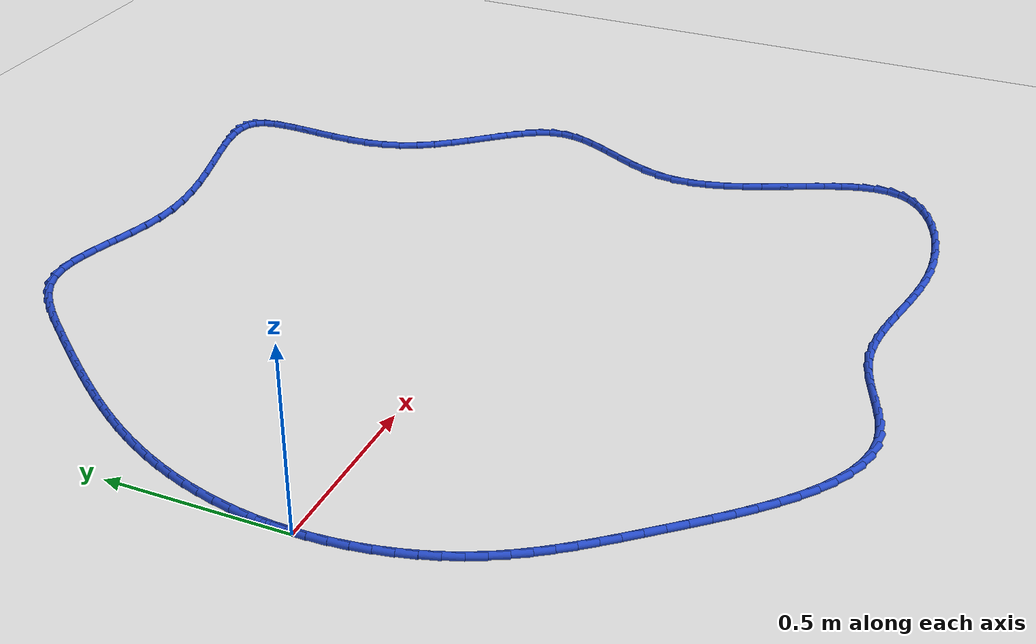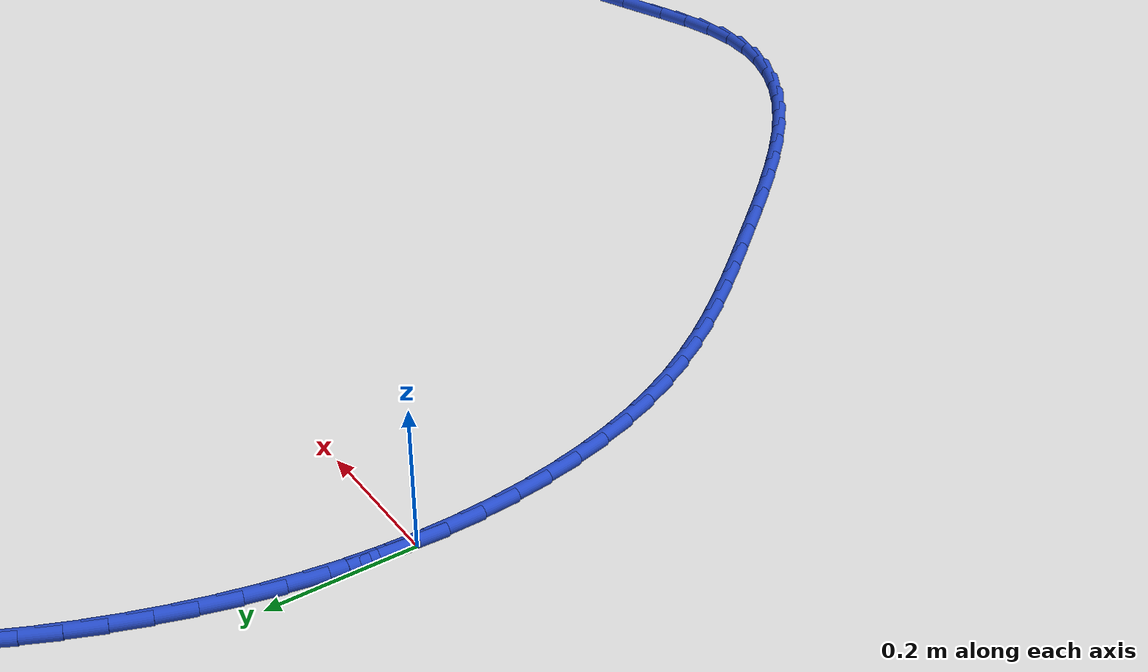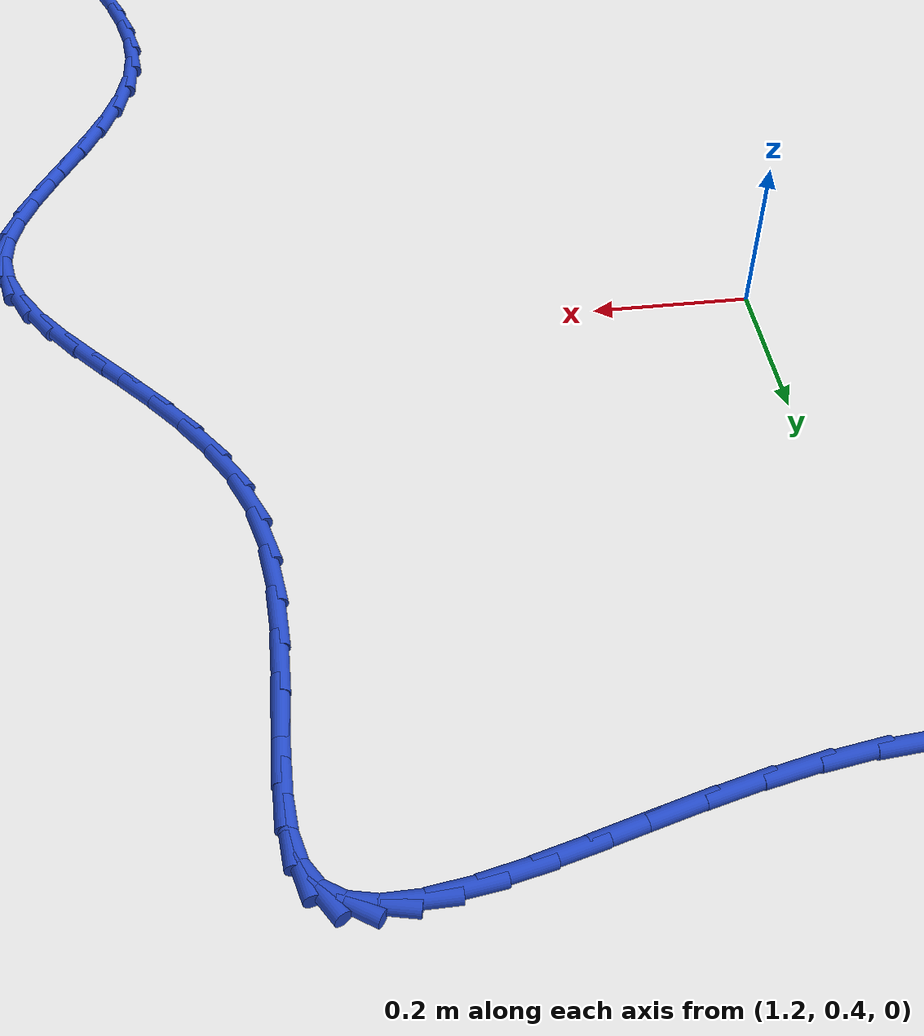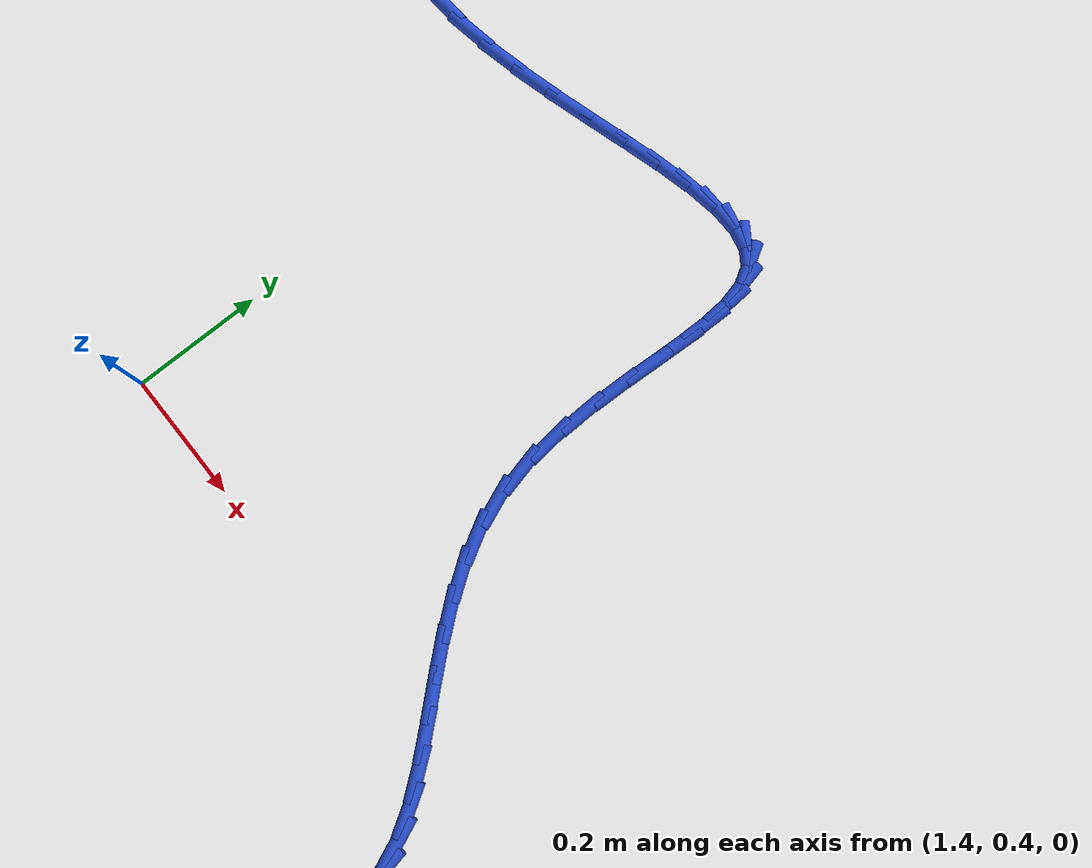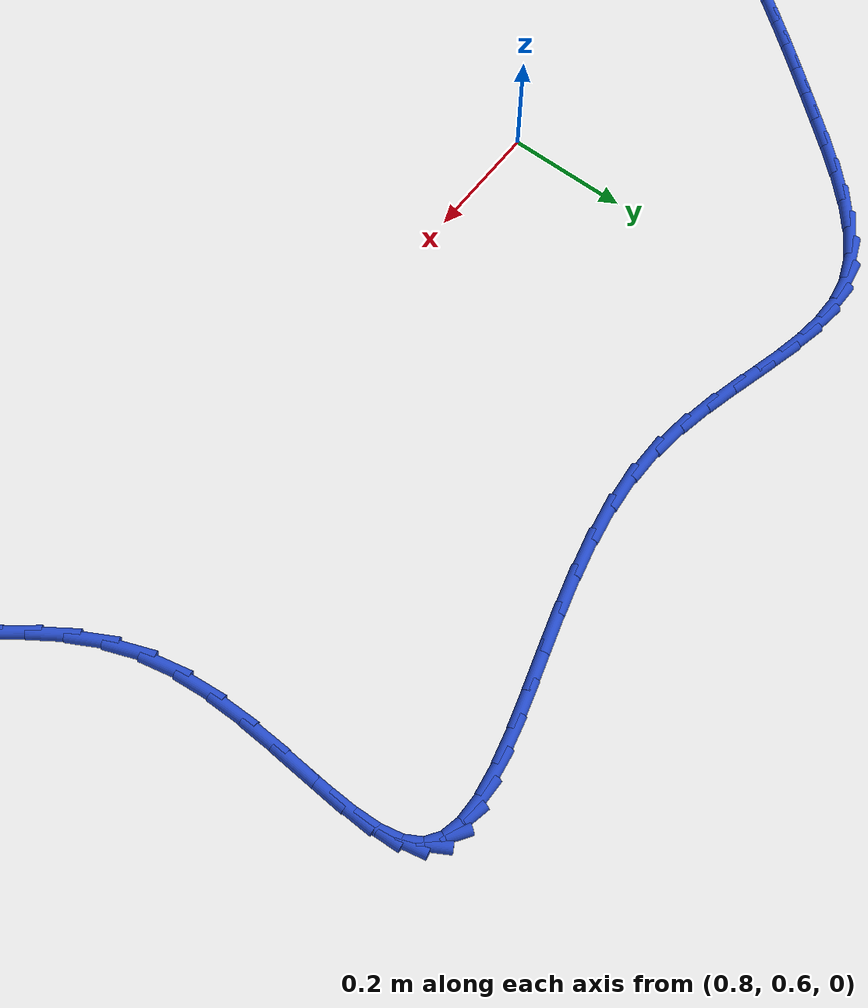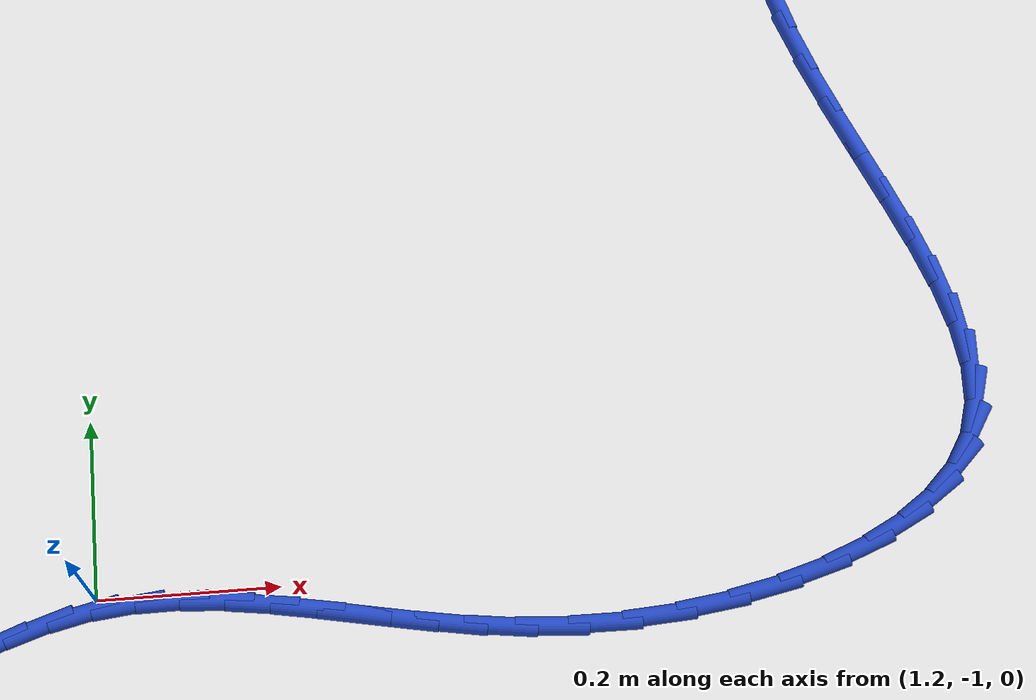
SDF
<sdf version="1.6">
 <world name="default">
  <light name="sun" type="directional">
   <pose>0 0 10 0 -0 0</pose>
   <diffuse>0.8 0.8 0.8 1</diffuse>
   <specular>0.2 0.2 0.2 1</specular>
   <attenuation>
    <range>1000</range>
    <constant>0.9</constant>
    <linear>0.01</linear>
    <quadratic>0.001</quadratic>
   </attenuation>
   <direction>-0.5 0.1 -0.9</direction>
  </light>
  <model name="ground_plane">
   <static>1</static>
   <link name="link">
    <collision name="collision">
     <geometry><plane><normal>0 0 1</normal><size>100 100</size></plane></geometry>
     <surface><friction><ode><mu>100</mu><mu2>50</mu2></ode></friction></surface>
    </collision>
    <visual name="visual">
     <cast_shadows>0</cast_shadows>
     <geometry><plane><normal>0 0 1</normal><size>100 100</size></plane></geometry>
     <material>
      <script><uri>file://media/materials/scripts/gazebo.material</uri><name>Gazebo/WhiteGlow</name></script>
     </material>
    </visual>
   </link>
  </model>
  <gravity>0 0 -9.8</gravity>
  <magnetic_field>6e-06 2.3e-05 -4.2e-05</magnetic_field>
  <atmosphere type="adiabatic"/>
  <physics name="default_physics" default="0" type="ode">
   <max_step_size>0.001</max_step_size>
   <real_time_factor>1</real_time_factor>
   <real_time_update_rate>1000</real_time_update_rate>
  </physics>
  <scene><ambient>0.4 0.4 0.4 1</ambient><background>0.7 0.7 0.7 1</background><shadows>1</shadows></scene>
  <spherical_coordinates>
   <surface_model>EARTH_WGS84</surface_model>
   <latitude_deg>0</latitude_deg>
   <longitude_deg>0</longitude_deg>
   <elevation>0</elevation>
   <heading_deg>0</heading_deg>
  </spherical_coordinates>
  <model name="line">
   <link name="link_0">
    <pose>2.42861286636753e-17 6.938893903907228e-17 0.01 0 1.57 1.533376814397982</pose>
    <collision name="collision">
     <geometry><cylinder><radius>0.01</radius><length>0.08</length></cylinder></geometry>
    </collision>
    <visual name="visual">
     <material>
      <script><name>Gazebo/Blue</name><uri>file://media/materials/scripts/gazebo.material</uri></script>
     </material>
     <geometry><cylinder><radius>0.01</radius><length>0.08</length></cylinder></geometry>
    </visual>
   </link>
   <link name="link_1">
    <pose>0.0019238145655279862 0.05138807101892818 0.01 0 1.57 1.4820030950396204</pose>
    <collision name="collision">
     <geometry><cylinder><radius>0.01</radius><length>0.08</length></cylinder></geometry>
    </collision>
    <visual name="visual">
     <material>
      <script><name>Gazebo/Blue</name><uri>file://media/materials/scripts/gazebo.material</uri></script>
     </material>
     <geometry><cylinder><radius>0.01</radius><length>0.08</length></cylinder></geometry>
    </visual>
   </link>
   <link name="link_2">
    <pose>0.006472638720636303 0.10248276716158493 0.01 0 1.57 1.432549027188589</pose>
    <collision name="collision">
     <geometry><cylinder><radius>0.01</radius><length>0.08</length></cylinder></geometry>
    </collision>
    <visual name="visual">
     <material>
      <script><name>Gazebo/Blue</name><uri>file://media/materials/scripts/gazebo.material</uri></script>
     </material>
     <geometry><cylinder><radius>0.01</radius><length>0.08</length></cylinder></geometry>
    </visual>
   </link>
   <link name="link_3">
    <pose>0.013523373232752885 0.15315832156864048 0.01 0 1.57 1.3848693728598331</pose>
    <collision name="collision">
     <geometry><cylinder><radius>0.01</radius><length>0.08</length></cylinder></geometry>
    </collision>
    <visual name="visual">
     <material>
      <script><name>Gazebo/Blue</name><uri>file://media/materials/scripts/gazebo.material</uri></script>
     </material>
     <geometry><cylinder><radius>0.01</radius><length>0.08</length></cylinder></geometry>
    </visual>
   </link>
   <link name="link_4">
    <pose>0.022952918869305672 0.20328896738076502 0.01 0 1.57 1.3387936132615557</pose>
    <collision name="collision">
     <geometry><cylinder><radius>0.01</radius><length>0.08</length></cylinder></geometry>
    </collision>
    <visual name="visual">
     <material>
      <script><name>Gazebo/Blue</name><uri>file://media/materials/scripts/gazebo.material</uri></script>
     </material>
     <geometry><cylinder><radius>0.01</radius><length>0.08</length></cylinder></geometry>
    </visual>
   </link>
   <link name="link_5">
    <pose>0.034638176397722535 0.25274893773862867 0.01 0 1.57 1.2941311945757217</pose>
    <collision name="collision">
     <geometry><cylinder><radius>0.01</radius><length>0.08</length></cylinder></geometry>
    </collision>
    <visual name="visual">
     <material>
      <script><name>Gazebo/Blue</name><uri>file://media/materials/scripts/gazebo.material</uri></script>
     </material>
     <geometry><cylinder><radius>0.01</radius><length>0.08</length></cylinder></geometry>
    </visual>
   </link>
   <link name="link_6">
    <pose>0.04845604658543143 0.30141246578290176 0.01 0 1.57 1.250675232409833</pose>
    <collision name="collision">
     <geometry><cylinder><radius>0.01</radius><length>0.08</length></cylinder></geometry>
    </collision>
    <visual name="visual">
     <material>
      <script><name>Gazebo/Blue</name><uri>file://media/materials/scripts/gazebo.material</uri></script>
     </material>
     <geometry><cylinder><radius>0.01</radius><length>0.08</length></cylinder></geometry>
    </visual>
   </link>
   <link name="link_7">
    <pose>0.06428343019986027 0.3491537846542544 0.01 0 1.57 1.2082047253122992</pose>
    <collision name="collision">
     <geometry><cylinder><radius>0.01</radius><length>0.08</length></cylinder></geometry>
    </collision>
    <visual name="visual">
     <material>
      <script><name>Gazebo/Blue</name><uri>file://media/materials/scripts/gazebo.material</uri></script>
     </material>
     <geometry><cylinder><radius>0.01</radius><length>0.08</length></cylinder></geometry>
    </visual>
   </link>
   <link name="link_8">
    <pose>0.08199722800843695 0.3958471274933568 0.01 0 1.57 1.1665765389644593</pose>
    <collision name="collision">
     <geometry><cylinder><radius>0.01</radius><length>0.08</length></cylinder></geometry>
    </collision>
    <visual name="visual">
     <material>
      <script><name>Gazebo/Blue</name><uri>file://media/materials/scripts/gazebo.material</uri></script>
     </material>
     <geometry><cylinder><radius>0.01</radius><length>0.08</length></cylinder></geometry>
    </visual>
   </link>
   <link name="link_9">
    <pose>0.10147762272994029 0.4413858772468075 0.01 0 1.57 1.126487077201281</pose>
    <collision name="collision">
     <geometry><cylinder><radius>0.01</radius><length>0.08</length></cylinder></geometry>
    </collision>
    <visual name="visual">
     <material>
      <script><name>Gazebo/Blue</name><uri>file://media/materials/scripts/gazebo.material</uri></script>
     </material>
     <geometry><cylinder><radius>0.01</radius><length>0.08</length></cylinder></geometry>
    </visual>
   </link>
   <link name="link_10">
    <pose>0.12263213767499846 0.48582294604732124 0.01 0 1.57 1.088625387109934</pose>
    <collision name="collision">
     <geometry><cylinder><radius>0.01</radius><length>0.08</length></cylinder></geometry>
    </collision>
    <visual name="visual">
     <material>
      <script><name>Gazebo/Blue</name><uri>file://media/materials/scripts/gazebo.material</uri></script>
     </material>
     <geometry><cylinder><radius>0.01</radius><length>0.08</length></cylinder></geometry>
    </visual>
   </link>
   <link name="link_11">
    <pose>0.1453818709373644 0.5292904533145479 0.01 0 1.57 1.0533178455263743</pose>
    <collision name="collision">
     <geometry><cylinder><radius>0.01</radius><length>0.08</length></cylinder></geometry>
    </collision>
    <visual name="visual">
     <material>
      <script><name>Gazebo/Blue</name><uri>file://media/materials/scripts/gazebo.material</uri></script>
     </material>
     <geometry><cylinder><radius>0.01</radius><length>0.08</length></cylinder></geometry>
    </visual>
   </link>
   <link name="link_12">
    <pose>0.16964801863178497 0.5719210904092823 0.01 0 1.57 1.0208235763637392</pose>
    <collision name="collision">
     <geometry><cylinder><radius>0.01</radius><length>0.08</length></cylinder></geometry>
    </collision>
    <visual name="visual">
     <material>
      <script><name>Gazebo/Blue</name><uri>file://media/materials/scripts/gazebo.material</uri></script>
     </material>
     <geometry><cylinder><radius>0.01</radius><length>0.08</length></cylinder></geometry>
    </visual>
   </link>
   <link name="link_13">
    <pose>0.1953517768730071 0.6138475486923185 0.01 0 1.57 0.9913363438492361</pose>
    <collision name="collision">
     <geometry><cylinder><radius>0.01</radius><length>0.08</length></cylinder></geometry>
    </collision>
    <visual name="visual">
     <material>
      <script><name>Gazebo/Blue</name><uri>file://media/materials/scripts/gazebo.material</uri></script>
     </material>
     <geometry><cylinder><radius>0.01</radius><length>0.08</length></cylinder></geometry>
    </visual>
   </link>
   <link name="link_14">
    <pose>0.22241434177577774 0.6552025195244515 0.01 0 1.57 0.9649876112297826</pose>
    <collision name="collision">
     <geometry><cylinder><radius>0.01</radius><length>0.08</length></cylinder></geometry>
    </collision>
    <visual name="visual">
     <material>
      <script><name>Gazebo/Blue</name><uri>file://media/materials/scripts/gazebo.material</uri></script>
     </material>
     <geometry><cylinder><radius>0.01</radius><length>0.08</length></cylinder></geometry>
    </visual>
   </link>
   <link name="link_15">
    <pose>0.2507569094548437 0.6961186942664758 0.01 0 1.57 0.9418523636959093</pose>
    <collision name="collision">
     <geometry><cylinder><radius>0.01</radius><length>0.08</length></cylinder></geometry>
    </collision>
    <visual name="visual">
     <material>
      <script><name>Gazebo/Blue</name><uri>file://media/materials/scripts/gazebo.material</uri></script>
     </material>
     <geometry><cylinder><radius>0.01</radius><length>0.08</length></cylinder></geometry>
    </visual>
   </link>
   <link name="link_16">
    <pose>0.280300676024952 0.736728764279186 0.01 0 1.57 0.9219565397747371</pose>
    <collision name="collision">
     <geometry><cylinder><radius>0.01</radius><length>0.08</length></cylinder></geometry>
    </collision>
    <visual name="visual">
     <material>
      <script><name>Gazebo/Blue</name><uri>file://media/materials/scripts/gazebo.material</uri></script>
     </material>
     <geometry><cylinder><radius>0.01</radius><length>0.08</length></cylinder></geometry>
    </visual>
   </link>
   <link name="link_17">
    <pose>0.3109668376008495 0.7771654209233767 0.01 0 1.57 0.9052850574311138</pose>
    <collision name="collision">
     <geometry><cylinder><radius>0.01</radius><length>0.08</length></cylinder></geometry>
    </collision>
    <visual name="visual">
     <material>
      <script><name>Gazebo/Blue</name><uri>file://media/materials/scripts/gazebo.material</uri></script>
     </material>
     <geometry><cylinder><radius>0.01</radius><length>0.08</length></cylinder></geometry>
    </visual>
   </link>
   <link name="link_18">
    <pose>0.3426765902972831 0.8175613555598423 0.01 0 1.57 0.8917896555122214</pose>
    <collision name="collision">
     <geometry><cylinder><radius>0.01</radius><length>0.08</length></cylinder></geometry>
    </collision>
    <visual name="visual">
     <material>
      <script><name>Gazebo/Blue</name><uri>file://media/materials/scripts/gazebo.material</uri></script>
     </material>
     <geometry><cylinder><radius>0.01</radius><length>0.08</length></cylinder></geometry>
    </visual>
   </link>
   <link name="link_19">
    <pose>0.3753511302289997 0.8580492595493772 0.01 0 1.57 0.8813960276539247</pose>
    <collision name="collision">
     <geometry><cylinder><radius>0.01</radius><length>0.08</length></cylinder></geometry>
    </collision>
    <visual name="visual">
     <material>
      <script><name>Gazebo/Blue</name><uri>file://media/materials/scripts/gazebo.material</uri></script>
     </material>
     <geometry><cylinder><radius>0.01</radius><length>0.08</length></cylinder></geometry>
    </visual>
   </link>
   <link name="link_20">
    <pose>0.40891165351074626 0.8987618242527766 0.01 0 1.57 0.8740099574078937</pose>
    <collision name="collision">
     <geometry><cylinder><radius>0.01</radius><length>0.08</length></cylinder></geometry>
    </collision>
    <visual name="visual">
     <material>
      <script><name>Gazebo/Blue</name><uri>file://media/materials/scripts/gazebo.material</uri></script>
     </material>
     <geometry><cylinder><radius>0.01</radius><length>0.08</length></cylinder></geometry>
    </visual>
   </link>
   <link name="link_21">
    <pose>0.4432793562572698 0.9398317410308346 0.01 0 1.57 0.8694918686294184</pose>
    <collision name="collision">
     <geometry><cylinder><radius>0.01</radius><length>0.08</length></cylinder></geometry>
    </collision>
    <visual name="visual">
     <material>
      <script><name>Gazebo/Blue</name><uri>file://media/materials/scripts/gazebo.material</uri></script>
     </material>
     <geometry><cylinder><radius>0.01</radius><length>0.08</length></cylinder></geometry>
    </visual>
   </link>
   <link name="link_22">
    <pose>0.4783756923124276 0.9813894368782488 0.01 0 1.57 0.8606278930769663</pose>
    <collision name="collision">
     <geometry><cylinder><radius>0.01</radius><length>0.08</length></cylinder></geometry>
    </collision>
    <visual name="visual">
     <material>
      <script><name>Gazebo/Blue</name><uri>file://media/materials/scripts/gazebo.material</uri></script>
     </material>
     <geometry><cylinder><radius>0.01</radius><length>0.08</length></cylinder></geometry>
    </visual>
   </link>
   <link name="link_23">
    <pose>0.5141825915619406 1.023034006110519 0.01 0 1.57 0.830725294610147</pose>
    <collision name="collision">
     <geometry><cylinder><radius>0.01</radius><length>0.08</length></cylinder></geometry>
    </collision>
    <visual name="visual">
     <material>
      <script><name>Gazebo/Blue</name><uri>file://media/materials/scripts/gazebo.material</uri></script>
     </material>
     <geometry><cylinder><radius>0.01</radius><length>0.08</length></cylinder></geometry>
    </visual>
   </link>
   <link name="link_24">
    <pose>0.5508198999830446 1.063152834668184 0.01 0 1.57 0.7747249734235946</pose>
    <collision name="collision">
     <geometry><cylinder><radius>0.01</radius><length>0.08</length></cylinder></geometry>
    </collision>
    <visual name="visual">
     <material>
      <script><name>Gazebo/Blue</name><uri>file://media/materials/scripts/gazebo.material</uri></script>
     </material>
     <geometry><cylinder><radius>0.01</radius><length>0.08</length></cylinder></geometry>
    </visual>
   </link>
   <link name="link_25">
    <pose>0.5884265962356536 1.099965211849976 0.01 0 1.57 0.6864911175497327</pose>
    <collision name="collision">
     <geometry><cylinder><radius>0.01</radius><length>0.08</length></cylinder></geometry>
    </collision>
    <visual name="visual">
     <material>
      <script><name>Gazebo/Blue</name><uri>file://media/materials/scripts/gazebo.material</uri></script>
     </material>
     <geometry><cylinder><radius>0.01</radius><length>0.08</length></cylinder></geometry>
    </visual>
   </link>
   <link name="link_26">
    <pose>0.6271416589796801 1.1316904269546262 0.01 0 1.57 0.5564521767941234</pose>
    <collision name="collision">
     <geometry><cylinder><radius>0.01</radius><length>0.08</length></cylinder></geometry>
    </collision>
    <visual name="visual">
     <material>
      <script><name>Gazebo/Blue</name><uri>file://media/materials/scripts/gazebo.material</uri></script>
     </material>
     <geometry><cylinder><radius>0.01</radius><length>0.08</length></cylinder></geometry>
    </visual>
   </link>
   <link name="link_27">
    <pose>0.6671040668750384 1.1565477692808674 0.01 0 1.57 0.3738827974162874</pose>
    <collision name="collision">
     <geometry><cylinder><radius>0.01</radius><length>0.08</length></cylinder></geometry>
    </collision>
    <visual name="visual">
     <material>
      <script><name>Gazebo/Blue</name><uri>file://media/materials/scripts/gazebo.material</uri></script>
     </material>
     <geometry><cylinder><radius>0.01</radius><length>0.08</length></cylinder></geometry>
    </visual>
   </link>
   <link name="link_28">
    <pose>0.7084524928693058 1.1727702800128634 0.01 0 1.57 0.16207478048670507</pose>
    <collision name="collision">
     <geometry><cylinder><radius>0.01</radius><length>0.08</length></cylinder></geometry>
    </collision>
    <visual name="visual">
     <material>
      <script><name>Gazebo/Blue</name><uri>file://media/materials/scripts/gazebo.material</uri></script>
     </material>
     <geometry><cylinder><radius>0.01</radius><length>0.08</length></cylinder></geometry>
    </visual>
   </link>
   <link name="link_29">
    <pose>0.7512992641866133 1.179776112379795 0.01 0 1.57 -0.016029814294842244</pose>
    <collision name="collision">
     <geometry><cylinder><radius>0.01</radius><length>0.08</length></cylinder></geometry>
    </collision>
    <visual name="visual">
     <material>
      <script><name>Gazebo/Blue</name><uri>file://media/materials/scripts/gazebo.material</uri></script>
     </material>
     <geometry><cylinder><radius>0.01</radius><length>0.08</length></cylinder></geometry>
    </visual>
   </link>
   <link name="link_30">
    <pose>0.7957104522537091 1.1790641483005242 0.01 0 1.57 -0.14494618474959392</pose>
    <collision name="collision">
     <geometry><cylinder><radius>0.01</radius><length>0.08</length></cylinder></geometry>
    </collision>
    <visual name="visual">
     <material>
      <script><name>Gazebo/Blue</name><uri>file://media/materials/scripts/gazebo.material</uri></script>
     </material>
     <geometry><cylinder><radius>0.01</radius><length>0.08</length></cylinder></geometry>
    </visual>
   </link>
   <link name="link_31">
    <pose>0.8417474408342993 1.1723441352617516 0.01 0 1.57 -0.226899189550946</pose>
    <collision name="collision">
     <geometry><cylinder><radius>0.01</radius><length>0.08</length></cylinder></geometry>
    </collision>
    <visual name="visual">
     <material>
      <script><name>Gazebo/Blue</name><uri>file://media/materials/scripts/gazebo.material</uri></script>
     </material>
     <geometry><cylinder><radius>0.01</radius><length>0.08</length></cylinder></geometry>
    </visual>
   </link>
   <link name="link_32">
    <pose>0.8894716136920893 1.1613258207501773 0.01 0 1.57 -0.268401252971268</pose>
    <collision name="collision">
     <geometry><cylinder><radius>0.01</radius><length>0.08</length></cylinder></geometry>
    </collision>
    <visual name="visual">
     <material>
      <script><name>Gazebo/Blue</name><uri>file://media/materials/scripts/gazebo.material</uri></script>
     </material>
     <geometry><cylinder><radius>0.01</radius><length>0.08</length></cylinder></geometry>
    </visual>
   </link>
   <link name="link_33">
    <pose>0.9389443545907854 1.1477189522525018 0.01 0 1.57 -0.275295002937172</pose>
    <collision name="collision">
     <geometry><cylinder><radius>0.01</radius><length>0.08</length></cylinder></geometry>
    </collision>
    <visual name="visual">
     <material>
      <script><name>Gazebo/Blue</name><uri>file://media/materials/scripts/gazebo.material</uri></script>
     </material>
     <geometry><cylinder><radius>0.01</radius><length>0.08</length></cylinder></geometry>
    </visual>
   </link>
   <link name="link_34">
    <pose>0.9902270472940934 1.1332332772554254 0.01 0 1.57 -0.25145270660123314</pose>
    <collision name="collision">
     <geometry><cylinder><radius>0.01</radius><length>0.08</length></cylinder></geometry>
    </collision>
    <visual name="visual">
     <material>
      <script><name>Gazebo/Blue</name><uri>file://media/materials/scripts/gazebo.material</uri></script>
     </material>
     <geometry><cylinder><radius>0.01</radius><length>0.08</length></cylinder></geometry>
    </visual>
   </link>
   <link name="link_35">
    <pose>1.0433810755657185 1.1195785432456482 0.01 0 1.57 -0.19908281637111164</pose>
    <collision name="collision">
     <geometry><cylinder><radius>0.01</radius><length>0.08</length></cylinder></geometry>
    </collision>
    <visual name="visual">
     <material>
      <script><name>Gazebo/Blue</name><uri>file://media/materials/scripts/gazebo.material</uri></script>
     </material>
     <geometry><cylinder><radius>0.01</radius><length>0.08</length></cylinder></geometry>
    </visual>
   </link>
   <link name="link_36">
    <pose>1.0984678231693672 1.10846449770987 0.01 0 1.57 -0.11966910587939088</pose>
    <collision name="collision">
     <geometry><cylinder><radius>0.01</radius><length>0.08</length></cylinder></geometry>
    </collision>
    <visual name="visual">
     <material>
      <script><name>Gazebo/Blue</name><uri>file://media/materials/scripts/gazebo.material</uri></script>
     </material>
     <geometry><cylinder><radius>0.01</radius><length>0.08</length></cylinder></geometry>
    </visual>
   </link>
   <link name="link_37">
    <pose>1.1555486738687453 1.1016008881347923 0.01 0 1.57 -0.015831266339124694</pose>
    <collision name="collision">
     <geometry><cylinder><radius>0.01</radius><length>0.08</length></cylinder></geometry>
    </collision>
    <visual name="visual">
     <material>
      <script><name>Gazebo/Blue</name><uri>file://media/materials/scripts/gazebo.material</uri></script>
     </material>
     <geometry><cylinder><radius>0.01</radius><length>0.08</length></cylinder></geometry>
    </visual>
   </link>
   <link name="link_38">
    <pose>1.2146753373398336 1.1006647599693775 0.01 0 1.57 0.08825302025232669</pose>
    <collision name="collision">
     <geometry><cylinder><radius>0.01</radius><length>0.08</length></cylinder></geometry>
    </collision>
    <visual name="visual">
     <material>
      <script><name>Gazebo/Blue</name><uri>file://media/materials/scripts/gazebo.material</uri></script>
     </material>
     <geometry><cylinder><radius>0.01</radius><length>0.08</length></cylinder></geometry>
    </visual>
   </link>
   <link name="link_39">
    <pose>1.2755194658612186 1.1060484223953055 0.01 0 1.57 0.16718868573415713</pose>
    <collision name="collision">
     <geometry><cylinder><radius>0.01</radius><length>0.08</length></cylinder></geometry>
    </collision>
    <visual name="visual">
     <material>
      <script><name>Gazebo/Blue</name><uri>file://media/materials/scripts/gazebo.material</uri></script>
     </material>
     <geometry><cylinder><radius>0.01</radius><length>0.08</length></cylinder></geometry>
    </visual>
   </link>
   <link name="link_40">
    <pose>1.3372566904134169 1.1164674469347995 0.01 0 1.57 0.22375195352338467</pose>
    <collision name="collision">
     <geometry><cylinder><radius>0.01</radius><length>0.08</length></cylinder></geometry>
    </collision>
    <visual name="visual">
     <material>
      <script><name>Gazebo/Blue</name><uri>file://media/materials/scripts/gazebo.material</uri></script>
     </material>
     <geometry><cylinder><radius>0.01</radius><length>0.08</length></cylinder></geometry>
    </visual>
   </link>
   <link name="link_41">
    <pose>1.3990292583135118 1.1305245558314034 0.01 0 1.57 0.26128451146765796</pose>
    <collision name="collision">
     <geometry><cylinder><radius>0.01</radius><length>0.08</length></cylinder></geometry>
    </collision>
    <visual name="visual">
     <material>
      <script><name>Gazebo/Blue</name><uri>file://media/materials/scripts/gazebo.material</uri></script>
     </material>
     <geometry><cylinder><radius>0.01</radius><length>0.08</length></cylinder></geometry>
    </visual>
   </link>
   <link name="link_42">
    <pose>1.4599794168785825 1.14682247132866 0.01 0 1.57 0.2815280647537304</pose>
    <collision name="collision">
     <geometry><cylinder><radius>0.01</radius><length>0.08</length></cylinder></geometry>
    </collision>
    <visual name="visual">
     <material>
      <script><name>Gazebo/Blue</name><uri>file://media/materials/scripts/gazebo.material</uri></script>
     </material>
     <geometry><cylinder><radius>0.01</radius><length>0.08</length></cylinder></geometry>
    </visual>
   </link>
   <link name="link_43">
    <pose>1.5192494134257106 1.1639639156701138 0.01 0 1.57 0.2844573885997822</pose>
    <collision name="collision">
     <geometry><cylinder><radius>0.01</radius><length>0.08</length></cylinder></geometry>
    </collision>
    <visual name="visual">
     <material>
      <script><name>Gazebo/Blue</name><uri>file://media/materials/scripts/gazebo.material</uri></script>
     </material>
     <geometry><cylinder><radius>0.01</radius><length>0.08</length></cylinder></geometry>
    </visual>
   </link>
   <link name="link_44">
    <pose>1.5759814952719768 1.1805516110993077 0.01 0 1.57 0.2678284771540373</pose>
    <collision name="collision">
     <geometry><cylinder><radius>0.01</radius><length>0.08</length></cylinder></geometry>
    </collision>
    <visual name="visual">
     <material>
      <script><name>Gazebo/Blue</name><uri>file://media/materials/scripts/gazebo.material</uri></script>
     </material>
     <geometry><cylinder><radius>0.01</radius><length>0.08</length></cylinder></geometry>
    </visual>
   </link>
   <link name="link_45">
    <pose>1.629317909734463 1.1951882798597862 0.01 0 1.57 0.22605437125081868</pose>
    <collision name="collision">
     <geometry><cylinder><radius>0.01</radius><length>0.08</length></cylinder></geometry>
    </collision>
    <visual name="visual">
     <material>
      <script><name>Gazebo/Blue</name><uri>file://media/materials/scripts/gazebo.material</uri></script>
     </material>
     <geometry><cylinder><radius>0.01</radius><length>0.08</length></cylinder></geometry>
    </visual>
   </link>
   <link name="link_46">
    <pose>1.6784009041302492 1.206476644195092 0.01 0 1.57 0.1477111433693948</pose>
    <collision name="collision">
     <geometry><cylinder><radius>0.01</radius><length>0.08</length></cylinder></geometry>
    </collision>
    <visual name="visual">
     <material>
      <script><name>Gazebo/Blue</name><uri>file://media/materials/scripts/gazebo.material</uri></script>
     </material>
     <geometry><cylinder><radius>0.01</radius><length>0.08</length></cylinder></geometry>
    </visual>
   </link>
   <link name="link_47">
    <pose>1.7223727257764168 1.2130194263487688 0.01 0 1.57 0.010523078331075587</pose>
    <collision name="collision">
     <geometry><cylinder><radius>0.01</radius><length>0.08</length></cylinder></geometry>
    </collision>
    <visual name="visual">
     <material>
      <script><name>Gazebo/Blue</name><uri>file://media/materials/scripts/gazebo.material</uri></script>
     </material>
     <geometry><cylinder><radius>0.01</radius><length>0.08</length></cylinder></geometry>
    </visual>
   </link>
   <link name="link_48">
    <pose>1.760375621990047 1.2134193485643607 0.01 0 1.57 -0.2251446801802223</pose>
    <collision name="collision">
     <geometry><cylinder><radius>0.01</radius><length>0.08</length></cylinder></geometry>
    </collision>
    <visual name="visual">
     <material>
      <script><name>Gazebo/Blue</name><uri>file://media/materials/scripts/gazebo.material</uri></script>
     </material>
     <geometry><cylinder><radius>0.01</radius><length>0.08</length></cylinder></geometry>
    </visual>
   </link>
   <link name="link_49">
    <pose>1.7915518400882209 1.206279133085411 0.01 0 1.57 -0.6001749595326926</pose>
    <collision name="collision">
     <geometry><cylinder><radius>0.01</radius><length>0.08</length></cylinder></geometry>
    </collision>
    <visual name="visual">
     <material>
      <script><name>Gazebo/Blue</name><uri>file://media/materials/scripts/gazebo.material</uri></script>
     </material>
     <geometry><cylinder><radius>0.01</radius><length>0.08</length></cylinder></geometry>
    </visual>
   </link>
   <link name="link_50">
    <pose>1.815043627388019 1.1902015021554633 0.01 0 1.57 -1.0426361062747604</pose>
    <collision name="collision">
     <geometry><cylinder><radius>0.01</radius><length>0.08</length></cylinder></geometry>
    </collision>
    <visual name="visual">
     <material>
      <script><name>Gazebo/Blue</name><uri>file://media/materials/scripts/gazebo.material</uri></script>
     </material>
     <geometry><cylinder><radius>0.01</radius><length>0.08</length></cylinder></geometry>
    </visual>
   </link>
   <link name="link_51">
    <pose>1.8302728174612575 1.1640994634006134 0.01 0 1.57 -1.3463260154593992</pose>
    <collision name="collision">
     <geometry><cylinder><radius>0.01</radius><length>0.08</length></cylinder></geometry>
    </collision>
    <visual name="visual">
     <material>
      <script><name>Gazebo/Blue</name><uri>file://media/materials/scripts/gazebo.material</uri></script>
     </material>
     <geometry><cylinder><radius>0.01</radius><length>0.08</length></cylinder></geometry>
    </visual>
   </link>
   <link name="link_52">
    <pose>1.8383431428510466 1.1287525992763086 0.01 0 1.57 -1.509618413375942</pose>
    <collision name="collision">
     <geometry><cylinder><radius>0.01</radius><length>0.08</length></cylinder></geometry>
    </collision>
    <visual name="visual">
     <material>
      <script><name>Gazebo/Blue</name><uri>file://media/materials/scripts/gazebo.material</uri></script>
     </material>
     <geometry><cylinder><radius>0.01</radius><length>0.08</length></cylinder></geometry>
    </visual>
   </link>
   <link name="link_53">
    <pose>1.8409842737178237 1.0856351590528233 0.01 0 1.57 1.5494013845881844</pose>
    <collision name="collision">
     <geometry><cylinder><radius>0.01</radius><length>0.08</length></cylinder></geometry>
    </collision>
    <visual name="visual">
     <material>
      <script><name>Gazebo/Blue</name><uri>file://media/materials/scripts/gazebo.material</uri></script>
     </material>
     <geometry><cylinder><radius>0.01</radius><length>0.08</length></cylinder></geometry>
    </visual>
   </link>
   <link name="link_54">
    <pose>1.8399269326820187 1.0362225600226287 0.01 0 1.57 1.5150738800068726</pose>
    <collision name="collision">
     <geometry><cylinder><radius>0.01</radius><length>0.08</length></cylinder></geometry>
    </collision>
    <visual name="visual">
     <material>
      <script><name>Gazebo/Blue</name><uri>file://media/materials/scripts/gazebo.material</uri></script>
     </material>
     <geometry><cylinder><radius>0.01</radius><length>0.08</length></cylinder></geometry>
    </visual>
   </link>
   <link name="link_55">
    <pose>1.8369018423640626 0.9819902194781968 0.01 0 1.57 1.5141999048447001</pose>
    <collision name="collision">
     <geometry><cylinder><radius>0.01</radius><length>0.08</length></cylinder></geometry>
    </collision>
    <visual name="visual">
     <material>
      <script><name>Gazebo/Blue</name><uri>file://media/materials/scripts/gazebo.material</uri></script>
     </material>
     <geometry><cylinder><radius>0.01</radius><length>0.08</length></cylinder></geometry>
    </visual>
   </link>
   <link name="link_56">
    <pose>1.8336397253843852 0.9244135547119975 0.01 0 1.57 1.5410565232010938</pose>
    <collision name="collision">
     <geometry><cylinder><radius>0.01</radius><length>0.08</length></cylinder></geometry>
    </collision>
    <visual name="visual">
     <material>
      <script><name>Gazebo/Blue</name><uri>file://media/materials/scripts/gazebo.material</uri></script>
     </material>
     <geometry><cylinder><radius>0.01</radius><length>0.08</length></cylinder></geometry>
    </visual>
   </link>
   <link name="link_57">
    <pose>1.8318713043634167 0.8649679830165024 0.01 0 1.57 -1.5464692352420188</pose>
    <collision name="collision">
     <geometry><cylinder><radius>0.01</radius><length>0.08</length></cylinder></geometry>
    </collision>
    <visual name="visual">
     <material>
      <script><name>Gazebo/Blue</name><uri>file://media/materials/scripts/gazebo.material</uri></script>
     </material>
     <geometry><cylinder><radius>0.01</radius><length>0.08</length></cylinder></geometry>
    </visual>
   </link>
   <link name="link_58">
    <pose>1.8333273019215874 0.8051289216841819 0.01 0 1.57 -1.4621137570448002</pose>
    <collision name="collision">
     <geometry><cylinder><radius>0.01</radius><length>0.08</length></cylinder></geometry>
    </collision>
    <visual name="visual">
     <material>
      <script><name>Gazebo/Blue</name><uri>file://media/materials/scripts/gazebo.material</uri></script>
     </material>
     <geometry><cylinder><radius>0.01</radius><length>0.08</length></cylinder></geometry>
    </visual>
   </link>
   <link name="link_59">
    <pose>1.839738440679327 0.7463717880075077 0.01 0 1.57 -1.3418417613071187</pose>
    <collision name="collision">
     <geometry><cylinder><radius>0.01</radius><length>0.08</length></cylinder></geometry>
    </collision>
    <visual name="visual">
     <material>
      <script><name>Gazebo/Blue</name><uri>file://media/materials/scripts/gazebo.material</uri></script>
     </material>
     <geometry><cylinder><radius>0.01</radius><length>0.08</length></cylinder></geometry>
    </visual>
   </link>
   <link name="link_60">
    <pose>1.8528353070375783 0.6901719222535345 0.01 0 1.57 -1.1936124835579938</pose>
    <collision name="collision">
     <geometry><cylinder><radius>0.01</radius><length>0.08</length></cylinder></geometry>
    </collision>
    <visual name="visual">
     <material>
      <script><name>Gazebo/Blue</name><uri>file://media/materials/scripts/gazebo.material</uri></script>
     </material>
     <geometry><cylinder><radius>0.01</radius><length>0.08</length></cylinder></geometry>
    </visual>
   </link>
   <link name="link_61">
    <pose>1.873656438040158 0.6376133448382011 0.01 0 1.57 -1.0639305635140832</pose>
    <collision name="collision">
     <geometry><cylinder><radius>0.01</radius><length>0.08</length></cylinder></geometry>
    </collision>
    <visual name="visual">
     <material>
      <script><name>Gazebo/Blue</name><uri>file://media/materials/scripts/gazebo.material</uri></script>
     </material>
     <geometry><cylinder><radius>0.01</radius><length>0.08</length></cylinder></geometry>
    </visual>
   </link>
   <link name="link_62">
    <pose>1.9009385920833592 0.5884785336380638 0.01 0 1.57 -0.9649855538932453</pose>
    <collision name="collision">
     <geometry><cylinder><radius>0.01</radius><length>0.08</length></cylinder></geometry>
    </collision>
    <visual name="visual">
     <material>
      <script><name>Gazebo/Blue</name><uri>file://media/materials/scripts/gazebo.material</uri></script>
     </material>
     <geometry><cylinder><radius>0.01</radius><length>0.08</length></cylinder></geometry>
    </visual>
   </link>
   <link name="link_63">
    <pose>1.9329405815972684 0.5422797116086805 0.01 0 1.57 -0.8963321040819026</pose>
    <collision name="collision">
     <geometry><cylinder><radius>0.01</radius><length>0.08</length></cylinder></geometry>
    </collision>
    <visual name="visual">
     <material>
      <script><name>Gazebo/Blue</name><uri>file://media/materials/scripts/gazebo.material</uri></script>
     </material>
     <geometry><cylinder><radius>0.01</radius><length>0.08</length></cylinder></geometry>
    </visual>
   </link>
   <link name="link_64">
    <pose>1.9679212190119701 0.4985291017056068 0.01 0 1.57 -0.8567063629016303</pose>
    <collision name="collision">
     <geometry><cylinder><radius>0.01</radius><length>0.08</length></cylinder></geometry>
    </collision>
    <visual name="visual">
     <material>
      <script><name>Gazebo/Blue</name><uri>file://media/materials/scripts/gazebo.material</uri></script>
     </material>
     <geometry><cylinder><radius>0.01</radius><length>0.08</length></cylinder></geometry>
    </visual>
   </link>
   <link name="link_65">
    <pose>2.004139316757548 0.45673892688439904 0.01 0 1.57 -0.8458666680850087</pose>
    <collision name="collision">
     <geometry><cylinder><radius>0.01</radius><length>0.08</length></cylinder></geometry>
    </collision>
    <visual name="visual">
     <material>
      <script><name>Gazebo/Blue</name><uri>file://media/materials/scripts/gazebo.material</uri></script>
     </material>
     <geometry><cylinder><radius>0.01</radius><length>0.08</length></cylinder></geometry>
    </visual>
   </link>
   <link name="link_66">
    <pose>2.0398536872640887 0.4164214101006139 0.01 0 1.57 -0.8657605929521367</pose>
    <collision name="collision">
     <geometry><cylinder><radius>0.01</radius><length>0.08</length></cylinder></geometry>
    </collision>
    <visual name="visual">
     <material>
      <script><name>Gazebo/Blue</name><uri>file://media/materials/scripts/gazebo.material</uri></script>
     </material>
     <geometry><cylinder><radius>0.01</radius><length>0.08</length></cylinder></geometry>
    </visual>
   </link>
   <link name="link_67">
    <pose>2.0733231429616756 0.3770887743098072 0.01 0 1.57 -0.9214426864944999</pose>
    <collision name="collision">
     <geometry><cylinder><radius>0.01</radius><length>0.08</length></cylinder></geometry>
    </collision>
    <visual name="visual">
     <material>
      <script><name>Gazebo/Blue</name><uri>file://media/materials/scripts/gazebo.material</uri></script>
     </material>
     <geometry><cylinder><radius>0.01</radius><length>0.08</length></cylinder></geometry>
    </visual>
   </link>
   <link name="link_68">
    <pose>2.102806496280394 0.338253242467536 0.01 0 1.57 -1.0217044409157192</pose>
    <collision name="collision">
     <geometry><cylinder><radius>0.01</radius><length>0.08</length></cylinder></geometry>
    </collision>
    <visual name="visual">
     <material>
      <script><name>Gazebo/Blue</name><uri>file://media/materials/scripts/gazebo.material</uri></script>
     </material>
     <geometry><cylinder><radius>0.01</radius><length>0.08</length></cylinder></geometry>
    </visual>
   </link>
   <link name="link_69">
    <pose>2.126562559650329 0.2994270375293566 0.01 0 1.57 -1.1779438364081947</pose>
    <collision name="collision">
     <geometry><cylinder><radius>0.01</radius><length>0.08</length></cylinder></geometry>
    </collision>
    <visual name="visual">
     <material>
      <script><name>Gazebo/Blue</name><uri>file://media/materials/scripts/gazebo.material</uri></script>
     </material>
     <geometry><cylinder><radius>0.01</radius><length>0.08</length></cylinder></geometry>
    </visual>
   </link>
   <link name="link_70">
    <pose>2.1428501455015656 0.2601223824508253 0.01 0 1.57 -1.3968154949582774</pose>
    <collision name="collision">
     <geometry><cylinder><radius>0.01</radius><length>0.08</length></cylinder></geometry>
    </collision>
    <visual name="visual">
     <material>
      <script><name>Gazebo/Blue</name><uri>file://media/materials/scripts/gazebo.material</uri></script>
     </material>
     <geometry><cylinder><radius>0.01</radius><length>0.08</length></cylinder></geometry>
    </visual>
   </link>
   <link name="link_71">
    <pose>2.149928066264188 0.219851500187498 0.01 0 1.57 1.490319147799225</pose>
    <collision name="collision">
     <geometry><cylinder><radius>0.01</radius><length>0.08</length></cylinder></geometry>
    </collision>
    <visual name="visual">
     <material>
      <script><name>Gazebo/Blue</name><uri>file://media/materials/scripts/gazebo.material</uri></script>
     </material>
     <geometry><cylinder><radius>0.01</radius><length>0.08</length></cylinder></geometry>
    </visual>
   </link>
   <link name="link_72">
    <pose>2.146568513683111 0.17819625469007658 0.01 0 1.57 1.2910727379119944</pose>
    <collision name="collision">
     <geometry><cylinder><radius>0.01</radius><length>0.08</length></cylinder></geometry>
    </collision>
    <visual name="visual">
     <material>
      <script><name>Gazebo/Blue</name><uri>file://media/materials/scripts/gazebo.material</uri></script>
     </material>
     <geometry><cylinder><radius>0.01</radius><length>0.08</length></cylinder></geometry>
    </visual>
   </link>
   <link name="link_73">
    <pose>2.1341881001240544 0.13509723118667571 0.01 0 1.57 1.1645805388480328</pose>
    <collision name="collision">
     <geometry><cylinder><radius>0.01</radius><length>0.08</length></cylinder></geometry>
    </collision>
    <visual name="visual">
     <material>
      <script><name>Gazebo/Blue</name><uri>file://media/materials/scripts/gazebo.material</uri></script>
     </material>
     <geometry><cylinder><radius>0.01</radius><length>0.08</length></cylinder></geometry>
    </visual>
   </link>
   <link name="link_74">
    <pose>2.115052465065341 0.09061018723767712 0.01 0 1.57 1.0947395931201396</pose>
    <collision name="collision">
     <geometry><cylinder><radius>0.01</radius><length>0.08</length></cylinder></geometry>
    </collision>
    <visual name="visual">
     <material>
      <script><name>Gazebo/Blue</name><uri>file://media/materials/scripts/gazebo.material</uri></script>
     </material>
     <geometry><cylinder><radius>0.01</radius><length>0.08</length></cylinder></geometry>
    </visual>
   </link>
   <link name="link_75">
    <pose>2.091427643241047 0.04479093402074577 0.01 0 1.57 1.0688442026982843</pose>
    <collision name="collision">
     <geometry><cylinder><radius>0.01</radius><length>0.08</length></cylinder></geometry>
    </collision>
    <visual name="visual">
     <material>
      <script><name>Gazebo/Blue</name><uri>file://media/materials/scripts/gazebo.material</uri></script>
     </material>
     <geometry><cylinder><radius>0.01</radius><length>0.08</length></cylinder></geometry>
    </visual>
   </link>
   <link name="link_76">
    <pose>2.0655796693852513 -0.002304717286453758 0.01 0 1.57 1.080252154869839</pose>
    <collision name="collision">
     <geometry><cylinder><radius>0.01</radius><length>0.08</length></cylinder></geometry>
    </collision>
    <visual name="visual">
     <material>
      <script><name>Gazebo/Blue</name><uri>file://media/materials/scripts/gazebo.material</uri></script>
     </material>
     <geometry><cylinder><radius>0.01</radius><length>0.08</length></cylinder></geometry>
    </visual>
   </link>
   <link name="link_77">
    <pose>2.0397745782320316 -0.0506209555062561 0.01 0 1.57 1.127468500062821</pose>
    <collision name="collision">
     <geometry><cylinder><radius>0.01</radius><length>0.08</length></cylinder></geometry>
    </collision>
    <visual name="visual">
     <material>
      <script><name>Gazebo/Blue</name><uri>file://media/materials/scripts/gazebo.material</uri></script>
     </material>
     <geometry><cylinder><radius>0.01</radius><length>0.08</length></cylinder></geometry>
    </visual>
   </link>
   <link name="link_78">
    <pose>2.0162784045154667 -0.10010196946099545 0.01 0 1.57 1.212892779780893</pose>
    <collision name="collision">
     <geometry><cylinder><radius>0.01</radius><length>0.08</length></cylinder></geometry>
    </collision>
    <visual name="visual">
     <material>
      <script><name>Gazebo/Blue</name><uri>file://media/materials/scripts/gazebo.material</uri></script>
     </material>
     <geometry><cylinder><radius>0.01</radius><length>0.08</length></cylinder></geometry>
    </visual>
   </link>
   <link name="link_79">
    <pose>1.9973571829696326 -0.1506919479730085 0.01 0 1.57 1.3410104180642233</pose>
    <collision name="collision">
     <geometry><cylinder><radius>0.01</radius><length>0.08</length></cylinder></geometry>
    </collision>
    <visual name="visual">
     <material>
      <script><name>Gazebo/Blue</name><uri>file://media/materials/scripts/gazebo.material</uri></script>
     </material>
     <geometry><cylinder><radius>0.01</radius><length>0.08</length></cylinder></geometry>
    </visual>
   </link>
   <link name="link_80">
    <pose>1.9852769483286072 -0.2023350798646285 0.01 0 1.57 1.5071200783496619</pose>
    <collision name="collision">
     <geometry><cylinder><radius>0.01</radius><length>0.08</length></cylinder></geometry>
    </collision>
    <visual name="visual">
     <material>
      <script><name>Gazebo/Blue</name><uri>file://media/materials/scripts/gazebo.material</uri></script>
     </material>
     <geometry><cylinder><radius>0.01</radius><length>0.08</length></cylinder></geometry>
    </visual>
   </link>
   <link name="link_81">
    <pose>1.9819221370940712 -0.2549492944069339 0.01 0 1.57 -1.480041740921945</pose>
    <collision name="collision">
     <geometry><cylinder><radius>0.01</radius><length>0.08</length></cylinder></geometry>
    </collision>
    <visual name="visual">
     <material>
      <script><name>Gazebo/Blue</name><uri>file://media/materials/scripts/gazebo.material</uri></script>
     </material>
     <geometry><cylinder><radius>0.01</radius><length>0.08</length></cylinder></geometry>
    </visual>
   </link>
   <link name="link_82">
    <pose>1.9867761389426344 -0.3082872936586517 0.01 0 1.57 -1.3579830776845279</pose>
    <collision name="collision">
     <geometry><cylinder><radius>0.01</radius><length>0.08</length></cylinder></geometry>
    </collision>
    <visual name="visual">
     <material>
      <script><name>Gazebo/Blue</name><uri>file://media/materials/scripts/gazebo.material</uri></script>
     </material>
     <geometry><cylinder><radius>0.01</radius><length>0.08</length></cylinder></geometry>
    </visual>
   </link>
   <link name="link_83">
    <pose>1.9983908049084405 -0.3620376761668724 0.01 0 1.57 -1.26627769424861</pose>
    <collision name="collision">
     <geometry><cylinder><radius>0.01</radius><length>0.08</length></cylinder></geometry>
    </collision>
    <visual name="visual">
     <material>
      <script><name>Gazebo/Blue</name><uri>file://media/materials/scripts/gazebo.material</uri></script>
     </material>
     <geometry><cylinder><radius>0.01</radius><length>0.08</length></cylinder></geometry>
    </visual>
   </link>
   <link name="link_84">
    <pose>2.015315933549539 -0.415888899238252 0.01 0 1.57 -1.2011170949893417</pose>
    <collision name="collision">
     <geometry><cylinder><radius>0.01</radius><length>0.08</length></cylinder></geometry>
    </collision>
    <visual name="visual">
     <material>
      <script><name>Gazebo/Blue</name><uri>file://media/materials/scripts/gazebo.material</uri></script>
     </material>
     <geometry><cylinder><radius>0.01</radius><length>0.08</length></cylinder></geometry>
    </visual>
   </link>
   <link name="link_85">
    <pose>2.0361013234239786 -0.4695294201794428 0.01 0 1.57 -1.1590781358711286</pose>
    <collision name="collision">
     <geometry><cylinder><radius>0.01</radius><length>0.08</length></cylinder></geometry>
    </collision>
    <visual name="visual">
     <material>
      <script><name>Gazebo/Blue</name><uri>file://media/materials/scripts/gazebo.material</uri></script>
     </material>
     <geometry><cylinder><radius>0.01</radius><length>0.08</length></cylinder></geometry>
    </visual>
   </link>
   <link name="link_86">
    <pose>2.0592967730898097 -0.522647696297101 0.01 0 1.57 -1.138010111799064</pose>
    <collision name="collision">
     <geometry><cylinder><radius>0.01</radius><length>0.08</length></cylinder></geometry>
    </collision>
    <visual name="visual">
     <material>
      <script><name>Gazebo/Blue</name><uri>file://media/materials/scripts/gazebo.material</uri></script>
     </material>
     <geometry><cylinder><radius>0.01</radius><length>0.08</length></cylinder></geometry>
    </visual>
   </link>
   <link name="link_87">
    <pose>2.083452081105079 -0.5749321848978793 0.01 0 1.57 -1.137385087495834</pose>
    <collision name="collision">
     <geometry><cylinder><radius>0.01</radius><length>0.08</length></cylinder></geometry>
    </collision>
    <visual name="visual">
     <material>
      <script><name>Gazebo/Blue</name><uri>file://media/materials/scripts/gazebo.material</uri></script>
     </material>
     <geometry><cylinder><radius>0.01</radius><length>0.08</length></cylinder></geometry>
    </visual>
   </link>
   <link name="link_88">
    <pose>2.107117046027837 -0.6260713432884318 0.01 0 1.57 -1.1585815289538592</pose>
    <collision name="collision">
     <geometry><cylinder><radius>0.01</radius><length>0.08</length></cylinder></geometry>
    </collision>
    <visual name="visual">
     <material>
      <script><name>Gazebo/Blue</name><uri>file://media/materials/scripts/gazebo.material</uri></script>
     </material>
     <geometry><cylinder><radius>0.01</radius><length>0.08</length></cylinder></geometry>
    </visual>
   </link>
   <link name="link_89">
    <pose>2.128841466416133 -0.6757536287754137 0.01 0 1.57 -1.2053460716630455</pose>
    <collision name="collision">
     <geometry><cylinder><radius>0.01</radius><length>0.08</length></cylinder></geometry>
    </collision>
    <visual name="visual">
     <material>
      <script><name>Gazebo/Blue</name><uri>file://media/materials/scripts/gazebo.material</uri></script>
     </material>
     <geometry><cylinder><radius>0.01</radius><length>0.08</length></cylinder></geometry>
    </visual>
   </link>
   <link name="link_90">
    <pose>2.147175140828014 -0.7236674986654787 0.01 0 1.57 -1.2845006244067267</pose>
    <collision name="collision">
     <geometry><cylinder><radius>0.01</radius><length>0.08</length></cylinder></geometry>
    </collision>
    <visual name="visual">
     <material>
      <script><name>Gazebo/Blue</name><uri>file://media/materials/scripts/gazebo.material</uri></script>
     </material>
     <geometry><cylinder><radius>0.01</radius><length>0.08</length></cylinder></geometry>
    </visual>
   </link>
   <link name="link_91">
    <pose>2.16066786782153 -0.7695014102652797 0.01 0 1.57 -1.406517302185844</pose>
    <collision name="collision">
     <geometry><cylinder><radius>0.01</radius><length>0.08</length></cylinder></geometry>
    </collision>
    <visual name="visual">
     <material>
      <script><name>Gazebo/Blue</name><uri>file://media/materials/scripts/gazebo.material</uri></script>
     </material>
     <geometry><cylinder><radius>0.01</radius><length>0.08</length></cylinder></geometry>
    </visual>
   </link>
   <link name="link_92">
    <pose>2.16786944595473 -0.8129438208814731 0.01 0 1.57 1.5575477019907449</pose>
    <collision name="collision">
     <geometry><cylinder><radius>0.01</radius><length>0.08</length></cylinder></geometry>
    </collision>
    <visual name="visual">
     <material>
      <script><name>Gazebo/Blue</name><uri>file://media/materials/scripts/gazebo.material</uri></script>
     </material>
     <geometry><cylinder><radius>0.01</radius><length>0.08</length></cylinder></geometry>
    </visual>
   </link>
   <link name="link_93">
    <pose>2.1673296737856633 -0.853683187820711 0.01 0 1.57 1.3183440323550255</pose>
    <collision name="collision">
     <geometry><cylinder><radius>0.01</radius><length>0.08</length></cylinder></geometry>
    </collision>
    <visual name="visual">
     <material>
      <script><name>Gazebo/Blue</name><uri>file://media/materials/scripts/gazebo.material</uri></script>
     </material>
     <geometry><cylinder><radius>0.01</radius><length>0.08</length></cylinder></geometry>
    </visual>
   </link>
   <link name="link_94">
    <pose>2.1575983498723788 -0.8914079683896493 0.01 0 1.57 1.04177745131362</pose>
    <collision name="collision">
     <geometry><cylinder><radius>0.01</radius><length>0.08</length></cylinder></geometry>
    </collision>
    <visual name="visual">
     <material>
      <script><name>Gazebo/Blue</name><uri>file://media/materials/scripts/gazebo.material</uri></script>
     </material>
     <geometry><cylinder><radius>0.01</radius><length>0.08</length></cylinder></geometry>
    </visual>
   </link>
   <link name="link_95">
    <pose>2.137478252434637 -0.9258248404817949 0.01 0 1.57 0.8028435392534158</pose>
    <collision name="collision">
     <geometry><cylinder><radius>0.01</radius><length>0.08</length></cylinder></geometry>
    </collision>
    <visual name="visual">
     <material>
      <script><name>Gazebo/Blue</name><uri>file://media/materials/scripts/gazebo.material</uri></script>
     </material>
     <geometry><cylinder><radius>0.01</radius><length>0.08</length></cylinder></geometry>
    </visual>
   </link>
   <link name="link_96">
    <pose>2.10759282752398 -0.9567716136244647 0.01 0 1.57 0.6213694327653867</pose>
    <collision name="collision">
     <geometry><cylinder><radius>0.01</radius><length>0.08</length></cylinder></geometry>
    </collision>
    <visual name="visual">
     <material>
      <script><name>Gazebo/Blue</name><uri>file://media/materials/scripts/gazebo.material</uri></script>
     </material>
     <geometry><cylinder><radius>0.01</radius><length>0.08</length></cylinder></geometry>
    </visual>
   </link>
   <link name="link_97">
    <pose>2.069362759053819 -0.9841435175407615 0.01 0 1.57 0.4832458283812483</pose>
    <collision name="collision">
     <geometry><cylinder><radius>0.01</radius><length>0.08</length></cylinder></geometry>
    </collision>
    <visual name="visual">
     <material>
      <script><name>Gazebo/Blue</name><uri>file://media/materials/scripts/gazebo.material</uri></script>
     </material>
     <geometry><cylinder><radius>0.01</radius><length>0.08</length></cylinder></geometry>
    </visual>
   </link>
   <link name="link_98">
    <pose>2.0242121059130165 -1.0078360250327483 0.01 0 1.57 0.3745299248284848</pose>
    <collision name="collision">
     <geometry><cylinder><radius>0.01</radius><length>0.08</length></cylinder></geometry>
    </collision>
    <visual name="visual">
     <material>
      <script><name>Gazebo/Blue</name><uri>file://media/materials/scripts/gazebo.material</uri></script>
     </material>
     <geometry><cylinder><radius>0.01</radius><length>0.08</length></cylinder></geometry>
    </visual>
   </link>
   <link name="link_99">
    <pose>1.9735649269904334 -1.0277446089024895 0.01 0 1.57 0.28480832232576725</pose>
    <collision name="collision">
     <geometry><cylinder><radius>0.01</radius><length>0.08</length></cylinder></geometry>
    </collision>
    <visual name="visual">
     <material>
      <script><name>Gazebo/Blue</name><uri>file://media/materials/scripts/gazebo.material</uri></script>
     </material>
     <geometry><cylinder><radius>0.01</radius><length>0.08</length></cylinder></geometry>
    </visual>
   </link>
   <link name="link_100">
    <pose>1.9188452811749304 -1.0437647419520482 0.01 0 1.57 0.20665599440319796</pose>
    <collision name="collision">
     <geometry><cylinder><radius>0.01</radius><length>0.08</length></cylinder></geometry>
    </collision>
    <visual name="visual">
     <material>
      <script><name>Gazebo/Blue</name><uri>file://media/materials/scripts/gazebo.material</uri></script>
     </material>
     <geometry><cylinder><radius>0.01</radius><length>0.08</length></cylinder></geometry>
    </visual>
   </link>
   <link name="link_101">
    <pose>1.8614772273553695 -1.0557918969834867 0.01 0 1.57 0.1345185043563749</pose>
    <collision name="collision">
     <geometry><cylinder><radius>0.01</radius><length>0.08</length></cylinder></geometry>
    </collision>
    <visual name="visual">
     <material>
      <script><name>Gazebo/Blue</name><uri>file://media/materials/scripts/gazebo.material</uri></script>
     </material>
     <geometry><cylinder><radius>0.01</radius><length>0.08</length></cylinder></geometry>
    </visual>
   </link>
   <link name="link_102">
    <pose>1.8028848244206113 -1.0637215467988703 0.01 0 1.57 0.06375054801562753</pose>
    <collision name="collision">
     <geometry><cylinder><radius>0.01</radius><length>0.08</length></cylinder></geometry>
    </collision>
    <visual name="visual">
     <material>
      <script><name>Gazebo/Blue</name><uri>file://media/materials/scripts/gazebo.material</uri></script>
     </material>
     <geometry><cylinder><radius>0.01</radius><length>0.08</length></cylinder></geometry>
    </visual>
   </link>
   <link name="link_103">
    <pose>1.7444921312595172 -1.0674491642002613 0.01 0 1.57 -0.009286748616456997</pose>
    <collision name="collision">
     <geometry><cylinder><radius>0.01</radius><length>0.08</length></cylinder></geometry>
    </collision>
    <visual name="visual">
     <material>
      <script><name>Gazebo/Blue</name><uri>file://media/materials/scripts/gazebo.material</uri></script>
     </material>
     <geometry><cylinder><radius>0.01</radius><length>0.08</length></cylinder></geometry>
    </visual>
   </link>
   <link name="link_104">
    <pose>1.6876434832823184 -1.0669212099196475 0.01 0 1.57 -0.07692014414634797</pose>
    <collision name="collision">
     <geometry><cylinder><radius>0.01</radius><length>0.08</length></cylinder></geometry>
    </collision>
    <visual name="visual">
     <material>
      <script><name>Gazebo/Blue</name><uri>file://media/materials/scripts/gazebo.material</uri></script>
     </material>
     <geometry><cylinder><radius>0.01</radius><length>0.08</length></cylinder></geometry>
    </visual>
   </link>
   <link name="link_105">
    <pose>1.6327368051105833 -1.062689430958518 0.01 0 1.57 -0.1306248242853461</pose>
    <collision name="collision">
     <geometry><cylinder><radius>0.01</radius><length>0.08</length></cylinder></geometry>
    </collision>
    <visual name="visual">
     <material>
      <script><name>Gazebo/Blue</name><uri>file://media/materials/scripts/gazebo.material</uri></script>
     </material>
     <geometry><cylinder><radius>0.01</radius><length>0.08</length></cylinder></geometry>
    </visual>
   </link>
   <link name="link_106">
    <pose>1.579549983821107 -1.05570212538997 0.01 0 1.57 -0.16836523836311182</pose>
    <collision name="collision">
     <geometry><cylinder><radius>0.01</radius><length>0.08</length></cylinder></geometry>
    </collision>
    <visual name="visual">
     <material>
      <script><name>Gazebo/Blue</name><uri>file://media/materials/scripts/gazebo.material</uri></script>
     </material>
     <geometry><cylinder><radius>0.01</radius><length>0.08</length></cylinder></geometry>
    </visual>
   </link>
   <link name="link_107">
    <pose>1.527850139552364 -1.046914477387734 0.01 0 1.57 -0.18868233667217796</pose>
    <collision name="collision">
     <geometry><cylinder><radius>0.01</radius><length>0.08</length></cylinder></geometry>
    </collision>
    <visual name="visual">
     <material>
      <script><name>Gazebo/Blue</name><uri>file://media/materials/scripts/gazebo.material</uri></script>
     </material>
     <geometry><cylinder><radius>0.01</radius><length>0.08</length></cylinder></geometry>
    </visual>
   </link>
   <link name="link_108">
    <pose>1.477404392442831 -1.0372816711255386 0.01 0 1.57 -0.19034069807098258</pose>
    <collision name="collision">
     <geometry><cylinder><radius>0.01</radius><length>0.08</length></cylinder></geometry>
    </collision>
    <visual name="visual">
     <material>
      <script><name>Gazebo/Blue</name><uri>file://media/materials/scripts/gazebo.material</uri></script>
     </material>
     <geometry><cylinder><radius>0.01</radius><length>0.08</length></cylinder></geometry>
    </visual>
   </link>
   <link name="link_109">
    <pose>1.4279798626309843 -1.0277588907771142 0.01 0 1.57 -0.17217289333436042</pose>
    <collision name="collision">
     <geometry><cylinder><radius>0.01</radius><length>0.08</length></cylinder></geometry>
    </collision>
    <visual name="visual">
     <material>
      <script><name>Gazebo/Blue</name><uri>file://media/materials/scripts/gazebo.material</uri></script>
     </material>
     <geometry><cylinder><radius>0.01</radius><length>0.08</length></cylinder></geometry>
    </visual>
   </link>
   <link name="link_110">
    <pose>1.3793436702552975 -1.0193013205161896 0.01 0 1.57 -0.1330912111526986</pose>
    <collision name="collision">
     <geometry><cylinder><radius>0.01</radius><length>0.08</length></cylinder></geometry>
    </collision>
    <visual name="visual">
     <material>
      <script><name>Gazebo/Blue</name><uri>file://media/materials/scripts/gazebo.material</uri></script>
     </material>
     <geometry><cylinder><radius>0.01</radius><length>0.08</length></cylinder></geometry>
    </visual>
   </link>
   <link name="link_111">
    <pose>1.331262935454247 -1.0128641445164939 0.01 0 1.57 -0.07235527600541183</pose>
    <collision name="collision">
     <geometry><cylinder><radius>0.01</radius><length>0.08</length></cylinder></geometry>
    </collision>
    <visual name="visual">
     <material>
      <script><name>Gazebo/Blue</name><uri>file://media/materials/scripts/gazebo.material</uri></script>
     </material>
     <geometry><cylinder><radius>0.01</radius><length>0.08</length></cylinder></geometry>
    </visual>
   </link>
   <link name="link_112">
    <pose>1.2835047783663094 -1.0094025469517574 0.01 0 1.57 0.009841935380691549</pose>
    <collision name="collision">
     <geometry><cylinder><radius>0.01</radius><length>0.08</length></cylinder></geometry>
    </collision>
    <visual name="visual">
     <material>
      <script><name>Gazebo/Blue</name><uri>file://media/materials/scripts/gazebo.material</uri></script>
     </material>
     <geometry><cylinder><radius>0.01</radius><length>0.08</length></cylinder></geometry>
    </visual>
   </link>
   <link name="link_113">
    <pose>1.2358363191299588 -1.0098717119957092 0.01 0 1.57 0.11153948072146375</pose>
    <collision name="collision">
     <geometry><cylinder><radius>0.01</radius><length>0.08</length></cylinder></geometry>
    </collision>
    <visual name="visual">
     <material>
      <script><name>Gazebo/Blue</name><uri>file://media/materials/scripts/gazebo.material</uri></script>
     </material>
     <geometry><cylinder><radius>0.01</radius><length>0.08</length></cylinder></geometry>
    </visual>
   </link>
   <link name="link_114">
    <pose>1.188024677883672 -1.0152268238220783 0.01 0 1.57 0.22579544968021023</pose>
    <collision name="collision">
     <geometry><cylinder><radius>0.01</radius><length>0.08</length></cylinder></geometry>
    </collision>
    <visual name="visual">
     <material>
      <script><name>Gazebo/Blue</name><uri>file://media/materials/scripts/gazebo.material</uri></script>
     </material>
     <geometry><cylinder><radius>0.01</radius><length>0.08</length></cylinder></geometry>
    </visual>
   </link>
   <link name="link_115">
    <pose>1.1398543854102814 -1.0262921489374468 0.01 0 1.57 0.3149908373540075</pose>
    <collision name="collision">
     <geometry><cylinder><radius>0.01</radius><length>0.08</length></cylinder></geometry>
    </collision>
    <visual name="visual">
     <material>
      <script><name>Gazebo/Blue</name><uri>file://media/materials/scripts/gazebo.material</uri></script>
     </material>
     <geometry><cylinder><radius>0.01</radius><length>0.08</length></cylinder></geometry>
    </visual>
   </link>
   <link name="link_116">
    <pose>1.091348652370933 -1.0420972234398191 0.01 0 1.57 0.3593186445592118</pose>
    <collision name="collision">
     <geometry><cylinder><radius>0.01</radius><length>0.08</length></cylinder></geometry>
    </collision>
    <visual name="visual">
     <material>
      <script><name>Gazebo/Blue</name><uri>file://media/materials/scripts/gazebo.material</uri></script>
     </material>
     <geometry><cylinder><radius>0.01</radius><length>0.08</length></cylinder></geometry>
    </visual>
   </link>
   <link name="link_117">
    <pose>1.0427038617501823 -1.0603694307826137 0.01 0 1.57 0.36271079567749837</pose>
    <collision name="collision">
     <geometry><cylinder><radius>0.01</radius><length>0.08</length></cylinder></geometry>
    </collision>
    <visual name="visual">
     <material>
      <script><name>Gazebo/Blue</name><uri>file://media/materials/scripts/gazebo.material</uri></script>
     </material>
     <geometry><cylinder><radius>0.01</radius><length>0.08</length></cylinder></geometry>
    </visual>
   </link>
   <link name="link_118">
    <pose>0.9941202814415946 -1.0788069422192692 0.01 0 1.57 0.32535237424503366</pose>
    <collision name="collision">
     <geometry><cylinder><radius>0.01</radius><length>0.08</length></cylinder></geometry>
    </collision>
    <visual name="visual">
     <material>
      <script><name>Gazebo/Blue</name><uri>file://media/materials/scripts/gazebo.material</uri></script>
     </material>
     <geometry><cylinder><radius>0.01</radius><length>0.08</length></cylinder></geometry>
    </visual>
   </link>
   <link name="link_119">
    <pose>0.9457981793387381 -1.0951079290032228 0.01 0 1.57 0.24296285530216954</pose>
    <collision name="collision">
     <geometry><cylinder><radius>0.01</radius><length>0.08</length></cylinder></geometry>
    </collision>
    <visual name="visual">
     <material>
      <script><name>Gazebo/Blue</name><uri>file://media/materials/scripts/gazebo.material</uri></script>
     </material>
     <geometry><cylinder><radius>0.01</radius><length>0.08</length></cylinder></geometry>
    </visual>
   </link>
   <link name="link_120">
    <pose>0.8979378233351779 -1.1069705623879131 0.01 0 1.57 0.10867791017385854</pose>
    <collision name="collision">
     <geometry><cylinder><radius>0.01</radius><length>0.08</length></cylinder></geometry>
    </collision>
    <visual name="visual">
     <material>
      <script><name>Gazebo/Blue</name><uri>file://media/materials/scripts/gazebo.material</uri></script>
     </material>
     <geometry><cylinder><radius>0.01</radius><length>0.08</length></cylinder></geometry>
    </visual>
   </link>
   <link name="link_121">
    <pose>0.8507377853215705 -1.1121204547960921 0.01 0 1.57 -0.056521974919145415</pose>
    <collision name="collision">
     <geometry><cylinder><radius>0.01</radius><length>0.08</length></cylinder></geometry>
    </collision>
    <visual name="visual">
     <material>
      <script><name>Gazebo/Blue</name><uri>file://media/materials/scripts/gazebo.material</uri></script>
     </material>
     <geometry><cylinder><radius>0.01</radius><length>0.08</length></cylinder></geometry>
    </visual>
   </link>
   <link name="link_122">
    <pose>0.8043217964989634 -1.1094941340457392 0.01 0 1.57 -0.2117293059381202</pose>
    <collision name="collision">
     <geometry><cylinder><radius>0.01</radius><length>0.08</length></cylinder></geometry>
    </collision>
    <visual name="visual">
     <material>
      <script><name>Gazebo/Blue</name><uri>file://media/materials/scripts/gazebo.material</uri></script>
     </material>
     <geometry><cylinder><radius>0.01</radius><length>0.08</length></cylinder></geometry>
    </visual>
   </link>
   <link name="link_123">
    <pose>0.7587108746402274 -1.0996900216669572 0.01 0 1.57 -0.34827598006246824</pose>
    <collision name="collision">
     <geometry><cylinder><radius>0.01</radius><length>0.08</length></cylinder></geometry>
    </collision>
    <visual name="visual">
     <material>
      <script><name>Gazebo/Blue</name><uri>file://media/materials/scripts/gazebo.material</uri></script>
     </material>
     <geometry><cylinder><radius>0.01</radius><length>0.08</length></cylinder></geometry>
    </visual>
   </link>
   <link name="link_124">
    <pose>0.7139185912370491 -1.0834270193266926 0.01 0 1.57 -0.4640652445597992</pose>
    <collision name="collision">
     <geometry><cylinder><radius>0.01</radius><length>0.08</length></cylinder></geometry>
    </collision>
    <visual name="visual">
     <material>
      <script><name>Gazebo/Blue</name><uri>file://media/materials/scripts/gazebo.material</uri></script>
     </material>
     <geometry><cylinder><radius>0.01</radius><length>0.08</length></cylinder></geometry>
    </visual>
   </link>
   <link name="link_125">
    <pose>0.6699585177811155 -1.0614240286918935 0.01 0 1.57 -0.5598933002124636</pose>
    <collision name="collision">
     <geometry><cylinder><radius>0.01</radius><length>0.08</length></cylinder></geometry>
    </collision>
    <visual name="visual">
     <material>
      <script><name>Gazebo/Blue</name><uri>file://media/materials/scripts/gazebo.material</uri></script>
     </material>
     <geometry><cylinder><radius>0.01</radius><length>0.08</length></cylinder></geometry>
    </visual>
   </link>
   <link name="link_126">
    <pose>0.6268442257641114 -1.0343999514295055 0.01 0 1.57 -0.6379506849779184</pose>
    <collision name="collision">
     <geometry><cylinder><radius>0.01</radius><length>0.08</length></cylinder></geometry>
    </collision>
    <visual name="visual">
     <material>
      <script><name>Gazebo/Blue</name><uri>file://media/materials/scripts/gazebo.material</uri></script>
     </material>
     <geometry><cylinder><radius>0.01</radius><length>0.08</length></cylinder></geometry>
    </visual>
   </link>
   <link name="link_127">
    <pose>0.5845892866777244 -1.0030736892064769 0.01 0 1.57 -0.7007622334379</pose>
    <collision name="collision">
     <geometry><cylinder><radius>0.01</radius><length>0.08</length></cylinder></geometry>
    </collision>
    <visual name="visual">
     <material>
      <script><name>Gazebo/Blue</name><uri>file://media/materials/scripts/gazebo.material</uri></script>
     </material>
     <geometry><cylinder><radius>0.01</radius><length>0.08</length></cylinder></geometry>
    </visual>
   </link>
   <link name="link_128">
    <pose>0.543207272013639 -0.9681641436897537 0.01 0 1.57 -0.7506400853175874</pose>
    <collision name="collision">
     <geometry><cylinder><radius>0.01</radius><length>0.08</length></cylinder></geometry>
    </collision>
    <visual name="visual">
     <material>
      <script><name>Gazebo/Blue</name><uri>file://media/materials/scripts/gazebo.material</uri></script>
     </material>
     <geometry><cylinder><radius>0.01</radius><length>0.08</length></cylinder></geometry>
    </visual>
   </link>
   <link name="link_129">
    <pose>0.5027117532635422 -0.9303902165462825 0.01 0 1.57 -0.7894722946073054</pose>
    <collision name="collision">
     <geometry><cylinder><radius>0.01</radius><length>0.08</length></cylinder></geometry>
    </collision>
    <visual name="visual">
     <material>
      <script><name>Gazebo/Blue</name><uri>file://media/materials/scripts/gazebo.material</uri></script>
     </material>
     <geometry><cylinder><radius>0.01</radius><length>0.08</length></cylinder></geometry>
    </visual>
   </link>
   <link name="link_130">
    <pose>0.46311630191912084 -0.8904708094430119 0.01 0 1.57 -0.8186764675960712</pose>
    <collision name="collision">
     <geometry><cylinder><radius>0.01</radius><length>0.08</length></cylinder></geometry>
    </collision>
    <visual name="visual">
     <material>
      <script><name>Gazebo/Blue</name><uri>file://media/materials/scripts/gazebo.material</uri></script>
     </material>
     <geometry><cylinder><radius>0.01</radius><length>0.08</length></cylinder></geometry>
    </visual>
   </link>
   <link name="link_131">
    <pose>0.4244344894720597 -0.8491248240468872 0.01 0 1.57 -0.8392135051508385</pose>
    <collision name="collision">
     <geometry><cylinder><radius>0.01</radius><length>0.08</length></cylinder></geometry>
    </collision>
    <visual name="visual">
     <material>
      <script><name>Gazebo/Blue</name><uri>file://media/materials/scripts/gazebo.material</uri></script>
     </material>
     <geometry><cylinder><radius>0.01</radius><length>0.08</length></cylinder></geometry>
    </visual>
   </link>
   <link name="link_132">
    <pose>0.38667988741404613 -0.8070711620248565 0.01 0 1.57 -0.8516069172100633</pose>
    <collision name="collision">
     <geometry><cylinder><radius>0.01</radius><length>0.08</length></cylinder></geometry>
    </collision>
    <visual name="visual">
     <material>
      <script><name>Gazebo/Blue</name><uri>file://media/materials/scripts/gazebo.material</uri></script>
     </material>
     <geometry><cylinder><radius>0.01</radius><length>0.08</length></cylinder></geometry>
    </visual>
   </link>
   <link name="link_133">
    <pose>0.349866067236765 -0.7650287250438652 0.01 0 1.57 -0.856212954215588</pose>
    <collision name="collision">
     <geometry><cylinder><radius>0.01</radius><length>0.08</length></cylinder></geometry>
    </collision>
    <visual name="visual">
     <material>
      <script><name>Gazebo/Blue</name><uri>file://media/materials/scripts/gazebo.material</uri></script>
     </material>
     <geometry><cylinder><radius>0.01</radius><length>0.08</length></cylinder></geometry>
    </visual>
   </link>
   <link name="link_134">
    <pose>0.31400980652398164 -0.7236972776649829 0.01 0 1.57 -0.8600077883990317</pose>
    <collision name="collision">
     <geometry><cylinder><radius>0.01</radius><length>0.08</length></cylinder></geometry>
    </collision>
    <visual name="visual">
     <material>
      <script><name>Gazebo/Blue</name><uri>file://media/materials/scripts/gazebo.material</uri></script>
     </material>
     <geometry><cylinder><radius>0.01</radius><length>0.08</length></cylinder></geometry>
    </visual>
   </link>
   <link name="link_135">
    <pose>0.27921164179173075 -0.6832766288909414 0.01 0 1.57 -0.8709687662210014</pose>
    <collision name="collision">
     <geometry><cylinder><radius>0.01</radius><length>0.08</length></cylinder></geometry>
    </collision>
    <visual name="visual">
     <material>
      <script><name>Gazebo/Blue</name><uri>file://media/materials/scripts/gazebo.material</uri></script>
     </material>
     <geometry><cylinder><radius>0.01</radius><length>0.08</length></cylinder></geometry>
    </visual>
   </link>
   <link name="link_136">
    <pose>0.24566184424522255 -0.6434309629807672 0.01 0 1.57 -0.8899234501237766</pose>
    <collision name="collision">
     <geometry><cylinder><radius>0.01</radius><length>0.08</length></cylinder></geometry>
    </collision>
    <visual name="visual">
     <material>
      <script><name>Gazebo/Blue</name><uri>file://media/materials/scripts/gazebo.material</uri></script>
     </material>
     <geometry><cylinder><radius>0.01</radius><length>0.08</length></cylinder></geometry>
    </visual>
   </link>
   <link name="link_137">
    <pose>0.21355508811273857 -0.6037981826280807 0.01 0 1.57 -0.9171964344634944</pose>
    <collision name="collision">
     <geometry><cylinder><radius>0.01</radius><length>0.08</length></cylinder></geometry>
    </collision>
    <visual name="visual">
     <material>
      <script><name>Gazebo/Blue</name><uri>file://media/materials/scripts/gazebo.material</uri></script>
     </material>
     <geometry><cylinder><radius>0.01</radius><length>0.08</length></cylinder></geometry>
    </visual>
   </link>
   <link name="link_138">
    <pose>0.18308604762256014 -0.5640161905265019 0.01 0 1.57 -0.952921871830834</pose>
    <collision name="collision">
     <geometry><cylinder><radius>0.01</radius><length>0.08</length></cylinder></geometry>
    </collision>
    <visual name="visual">
     <material>
      <script><name>Gazebo/Blue</name><uri>file://media/materials/scripts/gazebo.material</uri></script>
     </material>
     <geometry><cylinder><radius>0.01</radius><length>0.08</length></cylinder></geometry>
    </visual>
   </link>
   <link name="link_139">
    <pose>0.15444939700296703 -0.5237228893696487 0.01 0 1.57 -0.9969658473393616</pose>
    <collision name="collision">
     <geometry><cylinder><radius>0.01</radius><length>0.08</length></cylinder></geometry>
    </collision>
    <visual name="visual">
     <material>
      <script><name>Gazebo/Blue</name><uri>file://media/materials/scripts/gazebo.material</uri></script>
     </material>
     <geometry><cylinder><radius>0.01</radius><length>0.08</length></cylinder></geometry>
    </visual>
   </link>
   <link name="link_140">
    <pose>0.12783981048224116 -0.48255618185114196 0.01 0 1.57 -1.048845489865908</pose>
    <collision name="collision">
     <geometry><cylinder><radius>0.01</radius><length>0.08</length></cylinder></geometry>
    </collision>
    <visual name="visual">
     <material>
      <script><name>Gazebo/Blue</name><uri>file://media/materials/scripts/gazebo.material</uri></script>
     </material>
     <geometry><cylinder><radius>0.01</radius><length>0.08</length></cylinder></geometry>
    </visual>
   </link>
   <link name="link_141">
    <pose>0.10345196228866241 -0.4401539706645993 0.01 0 1.57 -1.1076472950754845</pose>
    <collision name="collision">
     <geometry><cylinder><radius>0.01</radius><length>0.08</length></cylinder></geometry>
    </collision>
    <visual name="visual">
     <material>
      <script><name>Gazebo/Blue</name><uri>file://media/materials/scripts/gazebo.material</uri></script>
     </material>
     <geometry><cylinder><radius>0.01</radius><length>0.08</length></cylinder></geometry>
    </visual>
   </link>
   <link name="link_142">
    <pose>0.08148014505362548 -0.39615550827354923 0.01 0 1.57 -1.1696159153019265</pose>
    <collision name="collision">
     <geometry><cylinder><radius>0.01</radius><length>0.08</length></cylinder></geometry>
    </collision>
    <visual name="visual">
     <material>
      <script><name>Gazebo/Blue</name><uri>file://media/materials/scripts/gazebo.material</uri></script>
     </material>
     <geometry><cylinder><radius>0.01</radius><length>0.08</length></cylinder></geometry>
    </visual>
   </link>
   <link name="link_143">
    <pose>0.06206580461763491 -0.3503869747885022 0.01 0 1.57 -1.22934402867702</pose>
    <collision name="collision">
     <geometry><cylinder><radius>0.01</radius><length>0.08</length></cylinder></geometry>
    </collision>
    <visual name="visual">
     <material>
      <script><name>Gazebo/Blue</name><uri>file://media/materials/scripts/gazebo.material</uri></script>
     </material>
     <geometry><cylinder><radius>0.01</radius><length>0.08</length></cylinder></geometry>
    </visual>
   </link>
   <link name="link_144">
    <pose>0.045243949574498094 -0.3030510360770192 0.01 0 1.57 -1.2867000420899937</pose>
    <collision name="collision">
     <geometry><cylinder><radius>0.01</radius><length>0.08</length></cylinder></geometry>
    </collision>
    <visual name="visual">
     <material>
      <script><name>Gazebo/Blue</name><uri>file://media/materials/scripts/gazebo.material</uri></script>
     </material>
     <geometry><cylinder><radius>0.01</radius><length>0.08</length></cylinder></geometry>
    </visual>
   </link>
   <link name="link_145">
    <pose>0.031036811842686765 -0.2543955511738702 0.01 0 1.57 -1.3421903759531122</pose>
    <collision name="collision">
     <geometry><cylinder><radius>0.01</radius><length>0.08</length></cylinder></geometry>
    </collision>
    <visual name="visual">
     <material>
      <script><name>Gazebo/Blue</name><uri>file://media/materials/scripts/gazebo.material</uri></script>
     </material>
     <geometry><cylinder><radius>0.01</radius><length>0.08</length></cylinder></geometry>
    </visual>
   </link>
   <link name="link_146">
    <pose>0.019466623340671656 -0.20466837911382124 0.01 0 1.57 -1.3963113250851402</pose>
    <collision name="collision">
     <geometry><cylinder><radius>0.01</radius><length>0.08</length></cylinder></geometry>
    </collision>
    <visual name="visual">
     <material>
      <script><name>Gazebo/Blue</name><uri>file://media/materials/scripts/gazebo.material</uri></script>
     </material>
     <geometry><cylinder><radius>0.01</radius><length>0.08</length></cylinder></geometry>
    </visual>
   </link>
   <link name="link_147">
    <pose>0.01055561598692423 -0.15411737893164143 0.01 0 1.57 -1.4495484370630427</pose>
    <collision name="collision">
     <geometry><cylinder><radius>0.01</radius><length>0.08</length></cylinder></geometry>
    </collision>
    <visual name="visual">
     <material>
      <script><name>Gazebo/Blue</name><uri>file://media/materials/scripts/gazebo.material</uri></script>
     </material>
     <geometry><cylinder><radius>0.01</radius><length>0.08</length></cylinder></geometry>
    </visual>
   </link>
   <link name="link_148">
    <pose>0.004326021699915767 -0.10299040966209982 0.01 0 1.57 -1.5023784762807884</pose>
    <collision name="collision">
     <geometry><cylinder><radius>0.01</radius><length>0.08</length></cylinder></geometry>
    </collision>
    <visual name="visual">
     <material>
      <script><name>Gazebo/Blue</name><uri>file://media/materials/scripts/gazebo.material</uri></script>
     </material>
     <geometry><cylinder><radius>0.01</radius><length>0.08</length></cylinder></geometry>
    </visual>
   </link>
   <link name="link_149">
    <pose>0.0008000723981172568 -0.05153533033996266 0.01 0 1.57 -1.5552728378601621</pose>
    <collision name="collision">
     <geometry><cylinder><radius>0.01</radius><length>0.08</length></cylinder></geometry>
    </collision>
    <visual name="visual">
     <material>
      <script><name>Gazebo/Blue</name><uri>file://media/materials/scripts/gazebo.material</uri></script>
     </material>
     <geometry><cylinder><radius>0.01</radius><length>0.08</length></cylinder></geometry>
    </visual>
   </link>
   <link name="link_150">
    <pose>1.0408340855860843e-17 1.3877787807814457e-16 0.01 0 1.57 1.5328911352714774</pose>
    <collision name="collision">
     <geometry><cylinder><radius>0.01</radius><length>0.08</length></cylinder></geometry>
    </collision>
    <visual name="visual">
     <material>
      <script><name>Gazebo/Blue</name><uri>file://media/materials/scripts/gazebo.material</uri></script>
     </material>
     <geometry><cylinder><radius>0.01</radius><length>0.08</length></cylinder></geometry>
    </visual>
   </link>
   <link name="link_151">
    <pose>0.0019480364240352672 0.05136772232302307 0.01 0 1.57 1.5328911352714776</pose>
    <collision name="collision">
     <geometry><cylinder><radius>0.01</radius><length>0.08</length></cylinder></geometry>
    </collision>
    <visual name="visual">
     <material>
      <script><name>Gazebo/Blue</name><uri>file://media/materials/scripts/gazebo.material</uri></script>
     </material>
     <geometry><cylinder><radius>0.01</radius><length>0.08</length></cylinder></geometry>
    </visual>
   </link>
  </model>
 </world>
</sdf>
